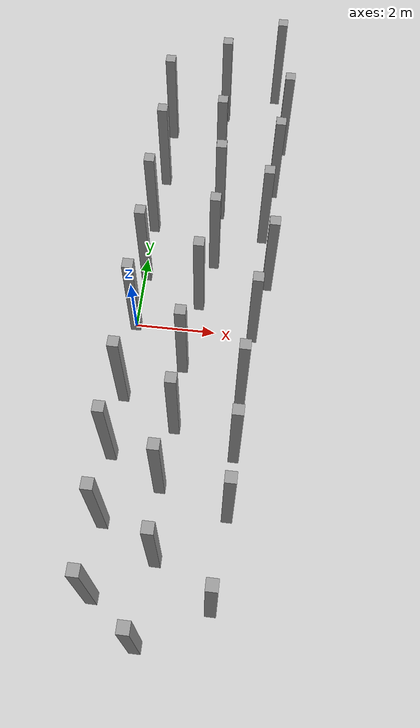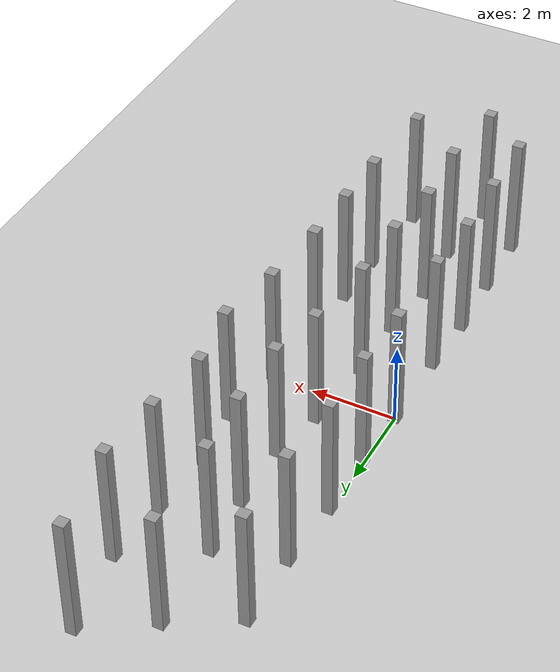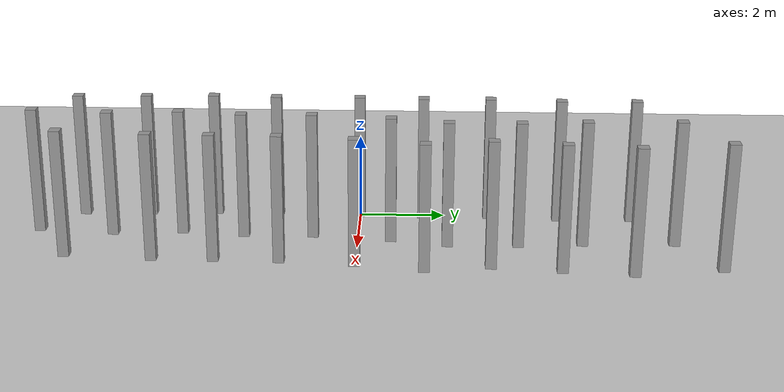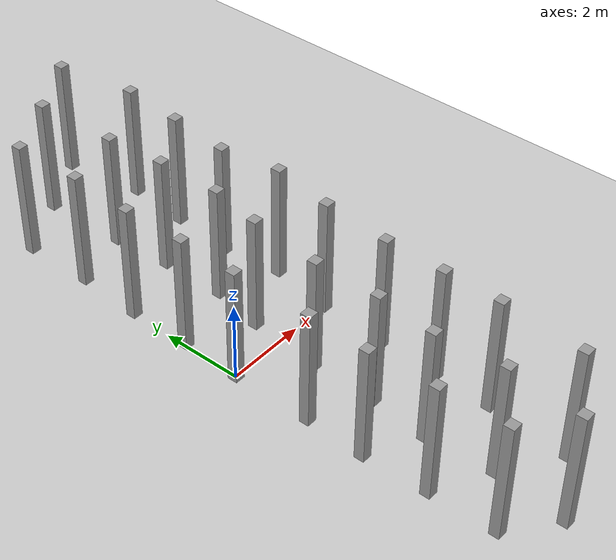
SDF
<sdf version="1.6">
 <world name="default">
  <light name="sun" type="directional">
   <pose>0 0 10 0 -0 0</pose>
   <diffuse>0.8 0.8 0.8 1</diffuse>
   <specular>0.1 0.1 0.1 1</specular>
   <attenuation>
    <range>1000</range>
    <constant>0.9</constant>
    <linear>0.01</linear>
    <quadratic>0.001</quadratic>
   </attenuation>
   <direction>-0.5 0.5 -1</direction>
  </light>
  <model name="ground_plane">
   <static>1</static>
   <link name="link">
    <collision name="collision">
     <geometry><plane><normal>0 0 1</normal><size>100 100</size></plane></geometry>
     <surface><friction><ode><mu>100</mu><mu2>50</mu2></ode></friction></surface>
    </collision>
    <visual name="visual">
     <cast_shadows>0</cast_shadows>
     <geometry><plane><normal>0 0 1</normal><size>100 100</size></plane></geometry>
     <material>
      <script><uri>file://media/materials/scripts/gazebo.material</uri><name>Gazebo/Grey</name></script>
     </material>
    </visual>
   </link>
  </model>
  <gravity>0 0 -9.8</gravity>
  <magnetic_field>6e-06 2.3e-05 -4.2e-05</magnetic_field>
  <atmosphere type="adiabatic"/>
  <physics name="default_physics" default="0" type="ode">
   <max_step_size>0.001</max_step_size>
   <real_time_factor>1</real_time_factor>
   <real_time_update_rate>1000</real_time_update_rate>
  </physics>
  <scene><ambient>0.4 0.4 0.4 1</ambient><background>0.7 0.7 0.7 1</background><shadows>1</shadows></scene>
  <spherical_coordinates>
   <surface_model>EARTH_WGS84</surface_model>
   <latitude_deg>0</latitude_deg>
   <longitude_deg>0</longitude_deg>
   <elevation>0</elevation>
   <heading_deg>0</heading_deg>
  </spherical_coordinates>
  <model name="box_2">
   <link name="link">
    <pose>0 0 1 0 -0 0</pose>
    <inertial>
     <mass>1</mass>
     <inertia><ixx>5.16667</ixx><ixy>0</ixy><ixz>0</ixz><iyy>5.16667</iyy><iyz>0</iyz><izz>5.16667</izz></inertia>
     <pose>0 0 1 0 -0 0</pose>
    </inertial>
    <visual name="ModelPreview_4::link::visual_1">
     <geometry><box><size>0.25 0.25 3</size></box></geometry>
     <material>
      <script><name>Gazebo/Grey</name><uri>file://media/materials/scripts/gazebo.material</uri></script>
      <ambient>0.3 0.3 0.3 1</ambient>
      <diffuse>0.7 0.7 0.7 1</diffuse>
      <specular>0.01 0.01 0.01 1</specular>
      <emissive>0 0 0 1</emissive>
      <shader type="vertex"><normal_map>__default__</normal_map></shader>
     </material>
    </visual>
    <visual name="visual">
     <geometry><box><size>0.25 0.25 3</size></box></geometry>
     <material>
      <script><name>Gazebo/Grey</name><uri>file://media/materials/scripts/gazebo.material</uri></script>
      <ambient>0.3 0.3 0.3 1</ambient>
      <diffuse>0.7 0.7 0.7 1</diffuse>
      <specular>0.01 0.01 0.01 1</specular>
      <emissive>0 0 0 1</emissive>
      <shader type="vertex"><normal_map>__default__</normal_map></shader>
     </material>
    </visual>
    <collision name="collision">
     <geometry><box><size>0.25 0.25 3</size></box></geometry>
     <surface>
      <friction>
       <ode><mu>1</mu><mu2>1</mu2><fdir1>0 0 0</fdir1><slip1>0</slip1><slip2>0</slip2></ode>
       <torsional>
        <coefficient>1</coefficient>
        <patch_radius>0</patch_radius>
        <surface_radius>0</surface_radius>
        <use_patch_radius>1</use_patch_radius>
        <ode><slip>0</slip></ode>
       </torsional>
      </friction>
      <bounce><restitution_coefficient>0</restitution_coefficient><threshold>1e+06</threshold></bounce>
      <contact>
       <collide_without_contact>0</collide_without_contact>
       <collide_without_contact_bitmask>1</collide_without_contact_bitmask>
       <collide_bitmask>1</collide_bitmask>
       <ode>
        <soft_cfm>0</soft_cfm>
        <soft_erp>0.2</soft_erp>
        <kp>1e+13</kp>
        <kd>1</kd>
        <max_vel>0.01</max_vel>
        <min_depth>0</min_depth>
       </ode>
       <bullet>
        <split_impulse>1</split_impulse>
        <split_impulse_penetration_threshold>-0.01</split_impulse_penetration_threshold>
        <soft_cfm>0</soft_cfm>
        <soft_erp>0.2</soft_erp>
        <kp>1e+13</kp>
        <kd>1</kd>
       </bullet>
      </contact>
     </surface>
    </collision>
   </link>
   <static>0</static>
   <pose>0.001306 -0.012782 0.5 0 0 -0.000121</pose>
  </model>
  <model name="box_2_0">
   <link name="link">
    <pose>0 0 1 0 -0 0</pose>
    <inertial>
     <mass>1</mass>
     <inertia><ixx>5.16667</ixx><ixy>0</ixy><ixz>0</ixz><iyy>5.16667</iyy><iyz>0</iyz><izz>5.16667</izz></inertia>
     <pose>0 0 1 0 -0 0</pose>
    </inertial>
    <visual name="ModelPreview_4::link::visual_1">
     <geometry><box><size>0.25 0.25 3</size></box></geometry>
     <material>
      <script><name>Gazebo/Grey</name><uri>file://media/materials/scripts/gazebo.material</uri></script>
      <ambient>0.3 0.3 0.3 1</ambient>
      <diffuse>0.7 0.7 0.7 1</diffuse>
      <specular>0.01 0.01 0.01 1</specular>
      <emissive>0 0 0 1</emissive>
      <shader type="vertex"><normal_map>__default__</normal_map></shader>
     </material>
    </visual>
    <visual name="visual">
     <geometry><box><size>0.25 0.25 3</size></box></geometry>
     <material>
      <script><name>Gazebo/Grey</name><uri>file://media/materials/scripts/gazebo.material</uri></script>
      <ambient>0.3 0.3 0.3 1</ambient>
      <diffuse>0.7 0.7 0.7 1</diffuse>
      <specular>0.01 0.01 0.01 1</specular>
      <emissive>0 0 0 1</emissive>
      <shader type="vertex"><normal_map>__default__</normal_map></shader>
     </material>
    </visual>
    <collision name="collision">
     <geometry><box><size>0.25 0.25 3</size></box></geometry>
     <surface>
      <friction>
       <ode><mu>1</mu><mu2>1</mu2><fdir1>0 0 0</fdir1><slip1>0</slip1><slip2>0</slip2></ode>
       <torsional>
        <coefficient>1</coefficient>
        <patch_radius>0</patch_radius>
        <surface_radius>0</surface_radius>
        <use_patch_radius>1</use_patch_radius>
        <ode><slip>0</slip></ode>
       </torsional>
      </friction>
      <bounce><restitution_coefficient>0</restitution_coefficient><threshold>1e+06</threshold></bounce>
      <contact>
       <collide_without_contact>0</collide_without_contact>
       <collide_without_contact_bitmask>1</collide_without_contact_bitmask>
       <collide_bitmask>1</collide_bitmask>
       <ode>
        <soft_cfm>0</soft_cfm>
        <soft_erp>0.2</soft_erp>
        <kp>1e+13</kp>
        <kd>1</kd>
        <max_vel>0.01</max_vel>
        <min_depth>0</min_depth>
       </ode>
       <bullet>
        <split_impulse>1</split_impulse>
        <split_impulse_penetration_threshold>-0.01</split_impulse_penetration_threshold>
        <soft_cfm>0</soft_cfm>
        <soft_erp>0.2</soft_erp>
        <kp>1e+13</kp>
        <kd>1</kd>
       </bullet>
      </contact>
     </surface>
    </collision>
   </link>
   <static>0</static>
   <pose>0.016184 -1.98397 0.5 -2e-06 -0 -0.000223</pose>
  </model>
  <model name="box_2_clone">
   <link name="link">
    <pose>0 0 1 0 -0 0</pose>
    <inertial>
     <mass>1</mass>
     <inertia><ixx>5.16667</ixx><ixy>0</ixy><ixz>0</ixz><iyy>5.16667</iyy><iyz>0</iyz><izz>5.16667</izz></inertia>
     <pose>0 0 1 0 -0 0</pose>
    </inertial>
    <visual name="ModelPreview_4::link::visual_1">
     <geometry><box><size>0.25 0.25 3</size></box></geometry>
     <material>
      <script><name>Gazebo/Grey</name><uri>file://media/materials/scripts/gazebo.material</uri></script>
      <ambient>0.3 0.3 0.3 1</ambient>
      <diffuse>0.7 0.7 0.7 1</diffuse>
      <specular>0.01 0.01 0.01 1</specular>
      <emissive>0 0 0 1</emissive>
      <shader type="vertex"><normal_map>__default__</normal_map></shader>
     </material>
    </visual>
    <visual name="visual">
     <geometry><box><size>0.25 0.25 3</size></box></geometry>
     <material>
      <script><name>Gazebo/Grey</name><uri>file://media/materials/scripts/gazebo.material</uri></script>
      <ambient>0.3 0.3 0.3 1</ambient>
      <diffuse>0.7 0.7 0.7 1</diffuse>
      <specular>0.01 0.01 0.01 1</specular>
      <emissive>0 0 0 1</emissive>
      <shader type="vertex"><normal_map>__default__</normal_map></shader>
     </material>
    </visual>
    <collision name="collision">
     <geometry><box><size>0.25 0.25 3</size></box></geometry>
     <surface>
      <friction>
       <ode><mu>1</mu><mu2>1</mu2><fdir1>0 0 0</fdir1><slip1>0</slip1><slip2>0</slip2></ode>
       <torsional>
        <coefficient>1</coefficient>
        <patch_radius>0</patch_radius>
        <surface_radius>0</surface_radius>
        <use_patch_radius>1</use_patch_radius>
        <ode><slip>0</slip></ode>
       </torsional>
      </friction>
      <bounce><restitution_coefficient>0</restitution_coefficient><threshold>1e+06</threshold></bounce>
      <contact>
       <collide_without_contact>0</collide_without_contact>
       <collide_without_contact_bitmask>1</collide_without_contact_bitmask>
       <collide_bitmask>1</collide_bitmask>
       <ode>
        <soft_cfm>0</soft_cfm>
        <soft_erp>0.2</soft_erp>
        <kp>1e+13</kp>
        <kd>1</kd>
        <max_vel>0.01</max_vel>
        <min_depth>0</min_depth>
       </ode>
       <bullet>
        <split_impulse>1</split_impulse>
        <split_impulse_penetration_threshold>-0.01</split_impulse_penetration_threshold>
        <soft_cfm>0</soft_cfm>
        <soft_erp>0.2</soft_erp>
        <kp>1e+13</kp>
        <kd>1</kd>
       </bullet>
      </contact>
     </surface>
    </collision>
   </link>
   <static>0</static>
   <pose>-0.030827 -3.47145 0.5 -2e-06 -0 -0.000164</pose>
  </model>
  <model name="box_2_clone_0">
   <link name="link">
    <pose>0 0 1 0 -0 0</pose>
    <inertial>
     <mass>1</mass>
     <inertia><ixx>5.16667</ixx><ixy>0</ixy><ixz>0</ixz><iyy>5.16667</iyy><iyz>0</iyz><izz>5.16667</izz></inertia>
     <pose>0 0 1 0 -0 0</pose>
    </inertial>
    <visual name="ModelPreview_4::link::visual_1">
     <geometry><box><size>0.25 0.25 3</size></box></geometry>
     <material>
      <script><name>Gazebo/Grey</name><uri>file://media/materials/scripts/gazebo.material</uri></script>
      <ambient>0.3 0.3 0.3 1</ambient>
      <diffuse>0.7 0.7 0.7 1</diffuse>
      <specular>0.01 0.01 0.01 1</specular>
      <emissive>0 0 0 1</emissive>
      <shader type="vertex"><normal_map>__default__</normal_map></shader>
     </material>
    </visual>
    <visual name="visual">
     <geometry><box><size>0.25 0.25 3</size></box></geometry>
     <material>
      <script><name>Gazebo/Grey</name><uri>file://media/materials/scripts/gazebo.material</uri></script>
      <ambient>0.3 0.3 0.3 1</ambient>
      <diffuse>0.7 0.7 0.7 1</diffuse>
      <specular>0.01 0.01 0.01 1</specular>
      <emissive>0 0 0 1</emissive>
      <shader type="vertex"><normal_map>__default__</normal_map></shader>
     </material>
    </visual>
    <collision name="collision">
     <geometry><box><size>0.25 0.25 3</size></box></geometry>
     <surface>
      <friction>
       <ode><mu>1</mu><mu2>1</mu2><fdir1>0 0 0</fdir1><slip1>0</slip1><slip2>0</slip2></ode>
       <torsional>
        <coefficient>1</coefficient>
        <patch_radius>0</patch_radius>
        <surface_radius>0</surface_radius>
        <use_patch_radius>1</use_patch_radius>
        <ode><slip>0</slip></ode>
       </torsional>
      </friction>
      <bounce><restitution_coefficient>0</restitution_coefficient><threshold>1e+06</threshold></bounce>
      <contact>
       <collide_without_contact>0</collide_without_contact>
       <collide_without_contact_bitmask>1</collide_without_contact_bitmask>
       <collide_bitmask>1</collide_bitmask>
       <ode>
        <soft_cfm>0</soft_cfm>
        <soft_erp>0.2</soft_erp>
        <kp>1e+13</kp>
        <kd>1</kd>
        <max_vel>0.01</max_vel>
        <min_depth>0</min_depth>
       </ode>
       <bullet>
        <split_impulse>1</split_impulse>
        <split_impulse_penetration_threshold>-0.01</split_impulse_penetration_threshold>
        <soft_cfm>0</soft_cfm>
        <soft_erp>0.2</soft_erp>
        <kp>1e+13</kp>
        <kd>1</kd>
       </bullet>
      </contact>
     </surface>
    </collision>
   </link>
   <static>0</static>
   <pose>0.044164 -5.06379 0.5 2e-06 -1e-06 -0.00013</pose>
  </model>
  <model name="box_2_clone_1">
   <link name="link">
    <pose>0 0 1 0 -0 0</pose>
    <inertial>
     <mass>1</mass>
     <inertia><ixx>5.16667</ixx><ixy>0</ixy><ixz>0</ixz><iyy>5.16667</iyy><iyz>0</iyz><izz>5.16667</izz></inertia>
     <pose>0 0 1 0 -0 0</pose>
    </inertial>
    <visual name="ModelPreview_4::link::visual_1">
     <geometry><box><size>0.25 0.25 3</size></box></geometry>
     <material>
      <script><name>Gazebo/Grey</name><uri>file://media/materials/scripts/gazebo.material</uri></script>
      <ambient>0.3 0.3 0.3 1</ambient>
      <diffuse>0.7 0.7 0.7 1</diffuse>
      <specular>0.01 0.01 0.01 1</specular>
      <emissive>0 0 0 1</emissive>
      <shader type="vertex"><normal_map>__default__</normal_map></shader>
     </material>
    </visual>
    <visual name="visual">
     <geometry><box><size>0.25 0.25 3</size></box></geometry>
     <material>
      <script><name>Gazebo/Grey</name><uri>file://media/materials/scripts/gazebo.material</uri></script>
      <ambient>0.3 0.3 0.3 1</ambient>
      <diffuse>0.7 0.7 0.7 1</diffuse>
      <specular>0.01 0.01 0.01 1</specular>
      <emissive>0 0 0 1</emissive>
      <shader type="vertex"><normal_map>__default__</normal_map></shader>
     </material>
    </visual>
    <collision name="collision">
     <geometry><box><size>0.25 0.25 3</size></box></geometry>
     <surface>
      <friction>
       <ode><mu>1</mu><mu2>1</mu2><fdir1>0 0 0</fdir1><slip1>0</slip1><slip2>0</slip2></ode>
       <torsional>
        <coefficient>1</coefficient>
        <patch_radius>0</patch_radius>
        <surface_radius>0</surface_radius>
        <use_patch_radius>1</use_patch_radius>
        <ode><slip>0</slip></ode>
       </torsional>
      </friction>
      <bounce><restitution_coefficient>0</restitution_coefficient><threshold>1e+06</threshold></bounce>
      <contact>
       <collide_without_contact>0</collide_without_contact>
       <collide_without_contact_bitmask>1</collide_without_contact_bitmask>
       <collide_bitmask>1</collide_bitmask>
       <ode>
        <soft_cfm>0</soft_cfm>
        <soft_erp>0.2</soft_erp>
        <kp>1e+13</kp>
        <kd>1</kd>
        <max_vel>0.01</max_vel>
        <min_depth>0</min_depth>
       </ode>
       <bullet>
        <split_impulse>1</split_impulse>
        <split_impulse_penetration_threshold>-0.01</split_impulse_penetration_threshold>
        <soft_cfm>0</soft_cfm>
        <soft_erp>0.2</soft_erp>
        <kp>1e+13</kp>
        <kd>1</kd>
       </bullet>
      </contact>
     </surface>
    </collision>
   </link>
   <static>0</static>
   <pose>0.048313 1.49751 0.5 0 0 -0.000186</pose>
  </model>
  <model name="box_2_clone_2">
   <link name="link">
    <pose>0 0 1 0 -0 0</pose>
    <inertial>
     <mass>1</mass>
     <inertia><ixx>5.16667</ixx><ixy>0</ixy><ixz>0</ixz><iyy>5.16667</iyy><iyz>0</iyz><izz>5.16667</izz></inertia>
     <pose>0 0 1 0 -0 0</pose>
    </inertial>
    <visual name="ModelPreview_4::link::visual_1">
     <geometry><box><size>0.25 0.25 3</size></box></geometry>
     <material>
      <script><name>Gazebo/Grey</name><uri>file://media/materials/scripts/gazebo.material</uri></script>
      <ambient>0.3 0.3 0.3 1</ambient>
      <diffuse>0.7 0.7 0.7 1</diffuse>
      <specular>0.01 0.01 0.01 1</specular>
      <emissive>0 0 0 1</emissive>
      <shader type="vertex"><normal_map>__default__</normal_map></shader>
     </material>
    </visual>
    <visual name="visual">
     <geometry><box><size>0.25 0.25 3</size></box></geometry>
     <material>
      <script><name>Gazebo/Grey</name><uri>file://media/materials/scripts/gazebo.material</uri></script>
      <ambient>0.3 0.3 0.3 1</ambient>
      <diffuse>0.7 0.7 0.7 1</diffuse>
      <specular>0.01 0.01 0.01 1</specular>
      <emissive>0 0 0 1</emissive>
      <shader type="vertex"><normal_map>__default__</normal_map></shader>
     </material>
    </visual>
    <collision name="collision">
     <geometry><box><size>0.25 0.25 3</size></box></geometry>
     <surface>
      <friction>
       <ode><mu>1</mu><mu2>1</mu2><fdir1>0 0 0</fdir1><slip1>0</slip1><slip2>0</slip2></ode>
       <torsional>
        <coefficient>1</coefficient>
        <patch_radius>0</patch_radius>
        <surface_radius>0</surface_radius>
        <use_patch_radius>1</use_patch_radius>
        <ode><slip>0</slip></ode>
       </torsional>
      </friction>
      <bounce><restitution_coefficient>0</restitution_coefficient><threshold>1e+06</threshold></bounce>
      <contact>
       <collide_without_contact>0</collide_without_contact>
       <collide_without_contact_bitmask>1</collide_without_contact_bitmask>
       <collide_bitmask>1</collide_bitmask>
       <ode>
        <soft_cfm>0</soft_cfm>
        <soft_erp>0.2</soft_erp>
        <kp>1e+13</kp>
        <kd>1</kd>
        <max_vel>0.01</max_vel>
        <min_depth>0</min_depth>
       </ode>
       <bullet>
        <split_impulse>1</split_impulse>
        <split_impulse_penetration_threshold>-0.01</split_impulse_penetration_threshold>
        <soft_cfm>0</soft_cfm>
        <soft_erp>0.2</soft_erp>
        <kp>1e+13</kp>
        <kd>1</kd>
       </bullet>
      </contact>
     </surface>
    </collision>
   </link>
   <static>0</static>
   <pose>0.031845 3.07004 0.5 0 0 -0.000171</pose>
  </model>
  <model name="box_2_clone_3">
   <link name="link">
    <pose>0 0 1 0 -0 0</pose>
    <inertial>
     <mass>1</mass>
     <inertia><ixx>5.16667</ixx><ixy>0</ixy><ixz>0</ixz><iyy>5.16667</iyy><iyz>0</iyz><izz>5.16667</izz></inertia>
     <pose>0 0 1 0 -0 0</pose>
    </inertial>
    <visual name="ModelPreview_4::link::visual_1">
     <geometry><box><size>0.25 0.25 3</size></box></geometry>
     <material>
      <script><name>Gazebo/Grey</name><uri>file://media/materials/scripts/gazebo.material</uri></script>
      <ambient>0.3 0.3 0.3 1</ambient>
      <diffuse>0.7 0.7 0.7 1</diffuse>
      <specular>0.01 0.01 0.01 1</specular>
      <emissive>0 0 0 1</emissive>
      <shader type="vertex"><normal_map>__default__</normal_map></shader>
     </material>
    </visual>
    <visual name="visual">
     <geometry><box><size>0.25 0.25 3</size></box></geometry>
     <material>
      <script><name>Gazebo/Grey</name><uri>file://media/materials/scripts/gazebo.material</uri></script>
      <ambient>0.3 0.3 0.3 1</ambient>
      <diffuse>0.7 0.7 0.7 1</diffuse>
      <specular>0.01 0.01 0.01 1</specular>
      <emissive>0 0 0 1</emissive>
      <shader type="vertex"><normal_map>__default__</normal_map></shader>
     </material>
    </visual>
    <collision name="collision">
     <geometry><box><size>0.25 0.25 3</size></box></geometry>
     <surface>
      <friction>
       <ode><mu>1</mu><mu2>1</mu2><fdir1>0 0 0</fdir1><slip1>0</slip1><slip2>0</slip2></ode>
       <torsional>
        <coefficient>1</coefficient>
        <patch_radius>0</patch_radius>
        <surface_radius>0</surface_radius>
        <use_patch_radius>1</use_patch_radius>
        <ode><slip>0</slip></ode>
       </torsional>
      </friction>
      <bounce><restitution_coefficient>0</restitution_coefficient><threshold>1e+06</threshold></bounce>
      <contact>
       <collide_without_contact>0</collide_without_contact>
       <collide_without_contact_bitmask>1</collide_without_contact_bitmask>
       <collide_bitmask>1</collide_bitmask>
       <ode>
        <soft_cfm>0</soft_cfm>
        <soft_erp>0.2</soft_erp>
        <kp>1e+13</kp>
        <kd>1</kd>
        <max_vel>0.01</max_vel>
        <min_depth>0</min_depth>
       </ode>
       <bullet>
        <split_impulse>1</split_impulse>
        <split_impulse_penetration_threshold>-0.01</split_impulse_penetration_threshold>
        <soft_cfm>0</soft_cfm>
        <soft_erp>0.2</soft_erp>
        <kp>1e+13</kp>
        <kd>1</kd>
       </bullet>
      </contact>
     </surface>
    </collision>
   </link>
   <static>0</static>
   <pose>0.124936 4.72453 0.500001 1e-06 3e-06 -9.4e-05</pose>
  </model>
  <model name="box_2_clone_4">
   <link name="link">
    <pose>0 0 1 0 -0 0</pose>
    <inertial>
     <mass>1</mass>
     <inertia><ixx>5.16667</ixx><ixy>0</ixy><ixz>0</ixz><iyy>5.16667</iyy><iyz>0</iyz><izz>5.16667</izz></inertia>
     <pose>0 0 1 0 -0 0</pose>
    </inertial>
    <visual name="ModelPreview_4::link::visual_1">
     <geometry><box><size>0.25 0.25 3</size></box></geometry>
     <material>
      <script><name>Gazebo/Grey</name><uri>file://media/materials/scripts/gazebo.material</uri></script>
      <ambient>0.3 0.3 0.3 1</ambient>
      <diffuse>0.7 0.7 0.7 1</diffuse>
      <specular>0.01 0.01 0.01 1</specular>
      <emissive>0 0 0 1</emissive>
      <shader type="vertex"><normal_map>__default__</normal_map></shader>
     </material>
    </visual>
    <visual name="visual">
     <geometry><box><size>0.25 0.25 3</size></box></geometry>
     <material>
      <script><name>Gazebo/Grey</name><uri>file://media/materials/scripts/gazebo.material</uri></script>
      <ambient>0.3 0.3 0.3 1</ambient>
      <diffuse>0.7 0.7 0.7 1</diffuse>
      <specular>0.01 0.01 0.01 1</specular>
      <emissive>0 0 0 1</emissive>
      <shader type="vertex"><normal_map>__default__</normal_map></shader>
     </material>
    </visual>
    <collision name="collision">
     <geometry><box><size>0.25 0.25 3</size></box></geometry>
     <surface>
      <friction>
       <ode><mu>1</mu><mu2>1</mu2><fdir1>0 0 0</fdir1><slip1>0</slip1><slip2>0</slip2></ode>
       <torsional>
        <coefficient>1</coefficient>
        <patch_radius>0</patch_radius>
        <surface_radius>0</surface_radius>
        <use_patch_radius>1</use_patch_radius>
        <ode><slip>0</slip></ode>
       </torsional>
      </friction>
      <bounce><restitution_coefficient>0</restitution_coefficient><threshold>1e+06</threshold></bounce>
      <contact>
       <collide_without_contact>0</collide_without_contact>
       <collide_without_contact_bitmask>1</collide_without_contact_bitmask>
       <collide_bitmask>1</collide_bitmask>
       <ode>
        <soft_cfm>0</soft_cfm>
        <soft_erp>0.2</soft_erp>
        <kp>1e+13</kp>
        <kd>1</kd>
        <max_vel>0.01</max_vel>
        <min_depth>0</min_depth>
       </ode>
       <bullet>
        <split_impulse>1</split_impulse>
        <split_impulse_penetration_threshold>-0.01</split_impulse_penetration_threshold>
        <soft_cfm>0</soft_cfm>
        <soft_erp>0.2</soft_erp>
        <kp>1e+13</kp>
        <kd>1</kd>
       </bullet>
      </contact>
     </surface>
    </collision>
   </link>
   <static>0</static>
   <pose>0.097978 6.47985 0.5 1e-06 -2e-06 -0.000149</pose>
  </model>
  <model name="box_2_clone_5">
   <link name="link">
    <pose>0 0 1 0 -0 0</pose>
    <inertial>
     <mass>1</mass>
     <inertia><ixx>5.16667</ixx><ixy>0</ixy><ixz>0</ixz><iyy>5.16667</iyy><iyz>0</iyz><izz>5.16667</izz></inertia>
     <pose>0 0 1 0 -0 0</pose>
    </inertial>
    <visual name="ModelPreview_4::link::visual_1">
     <geometry><box><size>0.25 0.25 3</size></box></geometry>
     <material>
      <script><name>Gazebo/Grey</name><uri>file://media/materials/scripts/gazebo.material</uri></script>
      <ambient>0.3 0.3 0.3 1</ambient>
      <diffuse>0.7 0.7 0.7 1</diffuse>
      <specular>0.01 0.01 0.01 1</specular>
      <emissive>0 0 0 1</emissive>
      <shader type="vertex"><normal_map>__default__</normal_map></shader>
     </material>
    </visual>
    <visual name="visual">
     <geometry><box><size>0.25 0.25 3</size></box></geometry>
     <material>
      <script><name>Gazebo/Grey</name><uri>file://media/materials/scripts/gazebo.material</uri></script>
      <ambient>0.3 0.3 0.3 1</ambient>
      <diffuse>0.7 0.7 0.7 1</diffuse>
      <specular>0.01 0.01 0.01 1</specular>
      <emissive>0 0 0 1</emissive>
      <shader type="vertex"><normal_map>__default__</normal_map></shader>
     </material>
    </visual>
    <collision name="collision">
     <geometry><box><size>0.25 0.25 3</size></box></geometry>
     <surface>
      <friction>
       <ode><mu>1</mu><mu2>1</mu2><fdir1>0 0 0</fdir1><slip1>0</slip1><slip2>0</slip2></ode>
       <torsional>
        <coefficient>1</coefficient>
        <patch_radius>0</patch_radius>
        <surface_radius>0</surface_radius>
        <use_patch_radius>1</use_patch_radius>
        <ode><slip>0</slip></ode>
       </torsional>
      </friction>
      <bounce><restitution_coefficient>0</restitution_coefficient><threshold>1e+06</threshold></bounce>
      <contact>
       <collide_without_contact>0</collide_without_contact>
       <collide_without_contact_bitmask>1</collide_without_contact_bitmask>
       <collide_bitmask>1</collide_bitmask>
       <ode>
        <soft_cfm>0</soft_cfm>
        <soft_erp>0.2</soft_erp>
        <kp>1e+13</kp>
        <kd>1</kd>
        <max_vel>0.01</max_vel>
        <min_depth>0</min_depth>
       </ode>
       <bullet>
        <split_impulse>1</split_impulse>
        <split_impulse_penetration_threshold>-0.01</split_impulse_penetration_threshold>
        <soft_cfm>0</soft_cfm>
        <soft_erp>0.2</soft_erp>
        <kp>1e+13</kp>
        <kd>1</kd>
       </bullet>
      </contact>
     </surface>
    </collision>
   </link>
   <static>0</static>
   <pose>0.096291 -6.6736 0.5 -2e-06 -1e-06 -9.9e-05</pose>
  </model>
  <model name="box_2_clone_1_clone">
   <link name="link">
    <pose>0 0 1 0 -0 0</pose>
    <inertial>
     <mass>1</mass>
     <inertia><ixx>5.16667</ixx><ixy>0</ixy><ixz>0</ixz><iyy>5.16667</iyy><iyz>0</iyz><izz>5.16667</izz></inertia>
     <pose>0 0 1 0 -0 0</pose>
    </inertial>
    <visual name="ModelPreview_4::link::visual_1">
     <geometry><box><size>0.25 0.25 3</size></box></geometry>
     <material>
      <script><name>Gazebo/Grey</name><uri>file://media/materials/scripts/gazebo.material</uri></script>
      <ambient>0.3 0.3 0.3 1</ambient>
      <diffuse>0.7 0.7 0.7 1</diffuse>
      <specular>0.01 0.01 0.01 1</specular>
      <emissive>0 0 0 1</emissive>
      <shader type="vertex"><normal_map>__default__</normal_map></shader>
     </material>
    </visual>
    <visual name="visual">
     <geometry><box><size>0.25 0.25 3</size></box></geometry>
     <material>
      <script><name>Gazebo/Grey</name><uri>file://media/materials/scripts/gazebo.material</uri></script>
      <ambient>0.3 0.3 0.3 1</ambient>
      <diffuse>0.7 0.7 0.7 1</diffuse>
      <specular>0.01 0.01 0.01 1</specular>
      <emissive>0 0 0 1</emissive>
      <shader type="vertex"><normal_map>__default__</normal_map></shader>
     </material>
    </visual>
    <collision name="collision">
     <geometry><box><size>0.25 0.25 3</size></box></geometry>
     <surface>
      <friction>
       <ode><mu>1</mu><mu2>1</mu2><fdir1>0 0 0</fdir1><slip1>0</slip1><slip2>0</slip2></ode>
       <torsional>
        <coefficient>1</coefficient>
        <patch_radius>0</patch_radius>
        <surface_radius>0</surface_radius>
        <use_patch_radius>1</use_patch_radius>
        <ode><slip>0</slip></ode>
       </torsional>
      </friction>
      <bounce><restitution_coefficient>0</restitution_coefficient><threshold>1e+06</threshold></bounce>
      <contact>
       <collide_without_contact>0</collide_without_contact>
       <collide_without_contact_bitmask>1</collide_without_contact_bitmask>
       <collide_bitmask>1</collide_bitmask>
       <ode>
        <soft_cfm>0</soft_cfm>
        <soft_erp>0.2</soft_erp>
        <kp>1e+13</kp>
        <kd>1</kd>
        <max_vel>0.01</max_vel>
        <min_depth>0</min_depth>
       </ode>
       <bullet>
        <split_impulse>1</split_impulse>
        <split_impulse_penetration_threshold>-0.01</split_impulse_penetration_threshold>
        <soft_cfm>0</soft_cfm>
        <soft_erp>0.2</soft_erp>
        <kp>1e+13</kp>
        <kd>1</kd>
       </bullet>
      </contact>
     </surface>
    </collision>
   </link>
   <static>0</static>
   <pose>1.77319 2.07182 0.5 1e-06 -0 -0.000176</pose>
  </model>
  <model name="box_2_clone_1_clone_0">
   <link name="link">
    <pose>0 0 1 0 -0 0</pose>
    <inertial>
     <mass>1</mass>
     <inertia><ixx>5.16667</ixx><ixy>0</ixy><ixz>0</ixz><iyy>5.16667</iyy><iyz>0</iyz><izz>5.16667</izz></inertia>
     <pose>0 0 1 0 -0 0</pose>
    </inertial>
    <visual name="ModelPreview_4::link::visual_1">
     <geometry><box><size>0.25 0.25 3</size></box></geometry>
     <material>
      <script><name>Gazebo/Grey</name><uri>file://media/materials/scripts/gazebo.material</uri></script>
      <ambient>0.3 0.3 0.3 1</ambient>
      <diffuse>0.7 0.7 0.7 1</diffuse>
      <specular>0.01 0.01 0.01 1</specular>
      <emissive>0 0 0 1</emissive>
      <shader type="vertex"><normal_map>__default__</normal_map></shader>
     </material>
    </visual>
    <visual name="visual">
     <geometry><box><size>0.25 0.25 3</size></box></geometry>
     <material>
      <script><name>Gazebo/Grey</name><uri>file://media/materials/scripts/gazebo.material</uri></script>
      <ambient>0.3 0.3 0.3 1</ambient>
      <diffuse>0.7 0.7 0.7 1</diffuse>
      <specular>0.01 0.01 0.01 1</specular>
      <emissive>0 0 0 1</emissive>
      <shader type="vertex"><normal_map>__default__</normal_map></shader>
     </material>
    </visual>
    <collision name="collision">
     <geometry><box><size>0.25 0.25 3</size></box></geometry>
     <surface>
      <friction>
       <ode><mu>1</mu><mu2>1</mu2><fdir1>0 0 0</fdir1><slip1>0</slip1><slip2>0</slip2></ode>
       <torsional>
        <coefficient>1</coefficient>
        <patch_radius>0</patch_radius>
        <surface_radius>0</surface_radius>
        <use_patch_radius>1</use_patch_radius>
        <ode><slip>0</slip></ode>
       </torsional>
      </friction>
      <bounce><restitution_coefficient>0</restitution_coefficient><threshold>1e+06</threshold></bounce>
      <contact>
       <collide_without_contact>0</collide_without_contact>
       <collide_without_contact_bitmask>1</collide_without_contact_bitmask>
       <collide_bitmask>1</collide_bitmask>
       <ode>
        <soft_cfm>0</soft_cfm>
        <soft_erp>0.2</soft_erp>
        <kp>1e+13</kp>
        <kd>1</kd>
        <max_vel>0.01</max_vel>
        <min_depth>0</min_depth>
       </ode>
       <bullet>
        <split_impulse>1</split_impulse>
        <split_impulse_penetration_threshold>-0.01</split_impulse_penetration_threshold>
        <soft_cfm>0</soft_cfm>
        <soft_erp>0.2</soft_erp>
        <kp>1e+13</kp>
        <kd>1</kd>
       </bullet>
      </contact>
     </surface>
    </collision>
   </link>
   <static>0</static>
   <pose>1.747 3.70529 0.5 -0 3e-06 -0.000185</pose>
  </model>
  <model name="box_2_clone_1_clone_1">
   <link name="link">
    <pose>0 0 1 0 -0 0</pose>
    <inertial>
     <mass>1</mass>
     <inertia><ixx>5.16667</ixx><ixy>0</ixy><ixz>0</ixz><iyy>5.16667</iyy><iyz>0</iyz><izz>5.16667</izz></inertia>
     <pose>0 0 1 0 -0 0</pose>
    </inertial>
    <visual name="ModelPreview_4::link::visual_1">
     <geometry><box><size>0.25 0.25 3</size></box></geometry>
     <material>
      <script><name>Gazebo/Grey</name><uri>file://media/materials/scripts/gazebo.material</uri></script>
      <ambient>0.3 0.3 0.3 1</ambient>
      <diffuse>0.7 0.7 0.7 1</diffuse>
      <specular>0.01 0.01 0.01 1</specular>
      <emissive>0 0 0 1</emissive>
      <shader type="vertex"><normal_map>__default__</normal_map></shader>
     </material>
    </visual>
    <visual name="visual">
     <geometry><box><size>0.25 0.25 3</size></box></geometry>
     <material>
      <script><name>Gazebo/Grey</name><uri>file://media/materials/scripts/gazebo.material</uri></script>
      <ambient>0.3 0.3 0.3 1</ambient>
      <diffuse>0.7 0.7 0.7 1</diffuse>
      <specular>0.01 0.01 0.01 1</specular>
      <emissive>0 0 0 1</emissive>
      <shader type="vertex"><normal_map>__default__</normal_map></shader>
     </material>
    </visual>
    <collision name="collision">
     <geometry><box><size>0.25 0.25 3</size></box></geometry>
     <surface>
      <friction>
       <ode><mu>1</mu><mu2>1</mu2><fdir1>0 0 0</fdir1><slip1>0</slip1><slip2>0</slip2></ode>
       <torsional>
        <coefficient>1</coefficient>
        <patch_radius>0</patch_radius>
        <surface_radius>0</surface_radius>
        <use_patch_radius>1</use_patch_radius>
        <ode><slip>0</slip></ode>
       </torsional>
      </friction>
      <bounce><restitution_coefficient>0</restitution_coefficient><threshold>1e+06</threshold></bounce>
      <contact>
       <collide_without_contact>0</collide_without_contact>
       <collide_without_contact_bitmask>1</collide_without_contact_bitmask>
       <collide_bitmask>1</collide_bitmask>
       <ode>
        <soft_cfm>0</soft_cfm>
        <soft_erp>0.2</soft_erp>
        <kp>1e+13</kp>
        <kd>1</kd>
        <max_vel>0.01</max_vel>
        <min_depth>0</min_depth>
       </ode>
       <bullet>
        <split_impulse>1</split_impulse>
        <split_impulse_penetration_threshold>-0.01</split_impulse_penetration_threshold>
        <soft_cfm>0</soft_cfm>
        <soft_erp>0.2</soft_erp>
        <kp>1e+13</kp>
        <kd>1</kd>
       </bullet>
      </contact>
     </surface>
    </collision>
   </link>
   <static>0</static>
   <pose>1.6256 5.19207 0.500001 -4e-06 -1e-06 -0.000196</pose>
  </model>
  <model name="box_2_clone_1_clone_2">
   <link name="link">
    <pose>0 0 1 0 -0 0</pose>
    <inertial>
     <mass>1</mass>
     <inertia><ixx>5.16667</ixx><ixy>0</ixy><ixz>0</ixz><iyy>5.16667</iyy><iyz>0</iyz><izz>5.16667</izz></inertia>
     <pose>0 0 1 0 -0 0</pose>
    </inertial>
    <visual name="ModelPreview_4::link::visual_1">
     <geometry><box><size>0.25 0.25 3</size></box></geometry>
     <material>
      <script><name>Gazebo/Grey</name><uri>file://media/materials/scripts/gazebo.material</uri></script>
      <ambient>0.3 0.3 0.3 1</ambient>
      <diffuse>0.7 0.7 0.7 1</diffuse>
      <specular>0.01 0.01 0.01 1</specular>
      <emissive>0 0 0 1</emissive>
      <shader type="vertex"><normal_map>__default__</normal_map></shader>
     </material>
    </visual>
    <visual name="visual">
     <geometry><box><size>0.25 0.25 3</size></box></geometry>
     <material>
      <script><name>Gazebo/Grey</name><uri>file://media/materials/scripts/gazebo.material</uri></script>
      <ambient>0.3 0.3 0.3 1</ambient>
      <diffuse>0.7 0.7 0.7 1</diffuse>
      <specular>0.01 0.01 0.01 1</specular>
      <emissive>0 0 0 1</emissive>
      <shader type="vertex"><normal_map>__default__</normal_map></shader>
     </material>
    </visual>
    <collision name="collision">
     <geometry><box><size>0.25 0.25 3</size></box></geometry>
     <surface>
      <friction>
       <ode><mu>1</mu><mu2>1</mu2><fdir1>0 0 0</fdir1><slip1>0</slip1><slip2>0</slip2></ode>
       <torsional>
        <coefficient>1</coefficient>
        <patch_radius>0</patch_radius>
        <surface_radius>0</surface_radius>
        <use_patch_radius>1</use_patch_radius>
        <ode><slip>0</slip></ode>
       </torsional>
      </friction>
      <bounce><restitution_coefficient>0</restitution_coefficient><threshold>1e+06</threshold></bounce>
      <contact>
       <collide_without_contact>0</collide_without_contact>
       <collide_without_contact_bitmask>1</collide_without_contact_bitmask>
       <collide_bitmask>1</collide_bitmask>
       <ode>
        <soft_cfm>0</soft_cfm>
        <soft_erp>0.2</soft_erp>
        <kp>1e+13</kp>
        <kd>1</kd>
        <max_vel>0.01</max_vel>
        <min_depth>0</min_depth>
       </ode>
       <bullet>
        <split_impulse>1</split_impulse>
        <split_impulse_penetration_threshold>-0.01</split_impulse_penetration_threshold>
        <soft_cfm>0</soft_cfm>
        <soft_erp>0.2</soft_erp>
        <kp>1e+13</kp>
        <kd>1</kd>
       </bullet>
      </contact>
     </surface>
    </collision>
   </link>
   <static>0</static>
   <pose>1.52668 0.763108 0.5 0 0 -0.000189</pose>
  </model>
  <model name="box_2_clone_1_clone_3">
   <link name="link">
    <pose>0 0 1 0 -0 0</pose>
    <inertial>
     <mass>1</mass>
     <inertia><ixx>5.16667</ixx><ixy>0</ixy><ixz>0</ixz><iyy>5.16667</iyy><iyz>0</iyz><izz>5.16667</izz></inertia>
     <pose>0 0 1 0 -0 0</pose>
    </inertial>
    <visual name="ModelPreview_4::link::visual_1">
     <geometry><box><size>0.25 0.25 3</size></box></geometry>
     <material>
      <script><name>Gazebo/Grey</name><uri>file://media/materials/scripts/gazebo.material</uri></script>
      <ambient>0.3 0.3 0.3 1</ambient>
      <diffuse>0.7 0.7 0.7 1</diffuse>
      <specular>0.01 0.01 0.01 1</specular>
      <emissive>0 0 0 1</emissive>
      <shader type="vertex"><normal_map>__default__</normal_map></shader>
     </material>
    </visual>
    <visual name="visual">
     <geometry><box><size>0.25 0.25 3</size></box></geometry>
     <material>
      <script><name>Gazebo/Grey</name><uri>file://media/materials/scripts/gazebo.material</uri></script>
      <ambient>0.3 0.3 0.3 1</ambient>
      <diffuse>0.7 0.7 0.7 1</diffuse>
      <specular>0.01 0.01 0.01 1</specular>
      <emissive>0 0 0 1</emissive>
      <shader type="vertex"><normal_map>__default__</normal_map></shader>
     </material>
    </visual>
    <collision name="collision">
     <geometry><box><size>0.25 0.25 3</size></box></geometry>
     <surface>
      <friction>
       <ode><mu>1</mu><mu2>1</mu2><fdir1>0 0 0</fdir1><slip1>0</slip1><slip2>0</slip2></ode>
       <torsional>
        <coefficient>1</coefficient>
        <patch_radius>0</patch_radius>
        <surface_radius>0</surface_radius>
        <use_patch_radius>1</use_patch_radius>
        <ode><slip>0</slip></ode>
       </torsional>
      </friction>
      <bounce><restitution_coefficient>0</restitution_coefficient><threshold>1e+06</threshold></bounce>
      <contact>
       <collide_without_contact>0</collide_without_contact>
       <collide_without_contact_bitmask>1</collide_without_contact_bitmask>
       <collide_bitmask>1</collide_bitmask>
       <ode>
        <soft_cfm>0</soft_cfm>
        <soft_erp>0.2</soft_erp>
        <kp>1e+13</kp>
        <kd>1</kd>
        <max_vel>0.01</max_vel>
        <min_depth>0</min_depth>
       </ode>
       <bullet>
        <split_impulse>1</split_impulse>
        <split_impulse_penetration_threshold>-0.01</split_impulse_penetration_threshold>
        <soft_cfm>0</soft_cfm>
        <soft_erp>0.2</soft_erp>
        <kp>1e+13</kp>
        <kd>1</kd>
       </bullet>
      </contact>
     </surface>
    </collision>
   </link>
   <static>0</static>
   <pose>1.33324 -1.05587 0.5 0 -2e-06 -0.000193</pose>
  </model>
  <model name="box_2_clone_1_clone_4">
   <link name="link">
    <pose>0 0 1 0 -0 0</pose>
    <inertial>
     <mass>1</mass>
     <inertia><ixx>5.16667</ixx><ixy>0</ixy><ixz>0</ixz><iyy>5.16667</iyy><iyz>0</iyz><izz>5.16667</izz></inertia>
     <pose>0 0 1 0 -0 0</pose>
    </inertial>
    <visual name="ModelPreview_4::link::visual_1">
     <geometry><box><size>0.25 0.25 3</size></box></geometry>
     <material>
      <script><name>Gazebo/Grey</name><uri>file://media/materials/scripts/gazebo.material</uri></script>
      <ambient>0.3 0.3 0.3 1</ambient>
      <diffuse>0.7 0.7 0.7 1</diffuse>
      <specular>0.01 0.01 0.01 1</specular>
      <emissive>0 0 0 1</emissive>
      <shader type="vertex"><normal_map>__default__</normal_map></shader>
     </material>
    </visual>
    <visual name="visual">
     <geometry><box><size>0.25 0.25 3</size></box></geometry>
     <material>
      <script><name>Gazebo/Grey</name><uri>file://media/materials/scripts/gazebo.material</uri></script>
      <ambient>0.3 0.3 0.3 1</ambient>
      <diffuse>0.7 0.7 0.7 1</diffuse>
      <specular>0.01 0.01 0.01 1</specular>
      <emissive>0 0 0 1</emissive>
      <shader type="vertex"><normal_map>__default__</normal_map></shader>
     </material>
    </visual>
    <collision name="collision">
     <geometry><box><size>0.25 0.25 3</size></box></geometry>
     <surface>
      <friction>
       <ode><mu>1</mu><mu2>1</mu2><fdir1>0 0 0</fdir1><slip1>0</slip1><slip2>0</slip2></ode>
       <torsional>
        <coefficient>1</coefficient>
        <patch_radius>0</patch_radius>
        <surface_radius>0</surface_radius>
        <use_patch_radius>1</use_patch_radius>
        <ode><slip>0</slip></ode>
       </torsional>
      </friction>
      <bounce><restitution_coefficient>0</restitution_coefficient><threshold>1e+06</threshold></bounce>
      <contact>
       <collide_without_contact>0</collide_without_contact>
       <collide_without_contact_bitmask>1</collide_without_contact_bitmask>
       <collide_bitmask>1</collide_bitmask>
       <ode>
        <soft_cfm>0</soft_cfm>
        <soft_erp>0.2</soft_erp>
        <kp>1e+13</kp>
        <kd>1</kd>
        <max_vel>0.01</max_vel>
        <min_depth>0</min_depth>
       </ode>
       <bullet>
        <split_impulse>1</split_impulse>
        <split_impulse_penetration_threshold>-0.01</split_impulse_penetration_threshold>
        <soft_cfm>0</soft_cfm>
        <soft_erp>0.2</soft_erp>
        <kp>1e+13</kp>
        <kd>1</kd>
       </bullet>
      </contact>
     </surface>
    </collision>
   </link>
   <static>0</static>
   <pose>1.34592 -2.67105 0.500001 0 -4e-06 -0.000177</pose>
  </model>
  <model name="box_2_clone_1_clone_5">
   <link name="link">
    <pose>0 0 1 0 -0 0</pose>
    <inertial>
     <mass>1</mass>
     <inertia><ixx>5.16667</ixx><ixy>0</ixy><ixz>0</ixz><iyy>5.16667</iyy><iyz>0</iyz><izz>5.16667</izz></inertia>
     <pose>0 0 1 0 -0 0</pose>
    </inertial>
    <visual name="ModelPreview_4::link::visual_1">
     <geometry><box><size>0.25 0.25 3</size></box></geometry>
     <material>
      <script><name>Gazebo/Grey</name><uri>file://media/materials/scripts/gazebo.material</uri></script>
      <ambient>0.3 0.3 0.3 1</ambient>
      <diffuse>0.7 0.7 0.7 1</diffuse>
      <specular>0.01 0.01 0.01 1</specular>
      <emissive>0 0 0 1</emissive>
      <shader type="vertex"><normal_map>__default__</normal_map></shader>
     </material>
    </visual>
    <visual name="visual">
     <geometry><box><size>0.25 0.25 3</size></box></geometry>
     <material>
      <script><name>Gazebo/Grey</name><uri>file://media/materials/scripts/gazebo.material</uri></script>
      <ambient>0.3 0.3 0.3 1</ambient>
      <diffuse>0.7 0.7 0.7 1</diffuse>
      <specular>0.01 0.01 0.01 1</specular>
      <emissive>0 0 0 1</emissive>
      <shader type="vertex"><normal_map>__default__</normal_map></shader>
     </material>
    </visual>
    <collision name="collision">
     <geometry><box><size>0.25 0.25 3</size></box></geometry>
     <surface>
      <friction>
       <ode><mu>1</mu><mu2>1</mu2><fdir1>0 0 0</fdir1><slip1>0</slip1><slip2>0</slip2></ode>
       <torsional>
        <coefficient>1</coefficient>
        <patch_radius>0</patch_radius>
        <surface_radius>0</surface_radius>
        <use_patch_radius>1</use_patch_radius>
        <ode><slip>0</slip></ode>
       </torsional>
      </friction>
      <bounce><restitution_coefficient>0</restitution_coefficient><threshold>1e+06</threshold></bounce>
      <contact>
       <collide_without_contact>0</collide_without_contact>
       <collide_without_contact_bitmask>1</collide_without_contact_bitmask>
       <collide_bitmask>1</collide_bitmask>
       <ode>
        <soft_cfm>0</soft_cfm>
        <soft_erp>0.2</soft_erp>
        <kp>1e+13</kp>
        <kd>1</kd>
        <max_vel>0.01</max_vel>
        <min_depth>0</min_depth>
       </ode>
       <bullet>
        <split_impulse>1</split_impulse>
        <split_impulse_penetration_threshold>-0.01</split_impulse_penetration_threshold>
        <soft_cfm>0</soft_cfm>
        <soft_erp>0.2</soft_erp>
        <kp>1e+13</kp>
        <kd>1</kd>
       </bullet>
      </contact>
     </surface>
    </collision>
   </link>
   <static>0</static>
   <pose>1.2015 -4.12952 0.500001 4e-06 7e-06 -0.000131</pose>
  </model>
  <model name="box_2_clone_1_clone_6">
   <link name="link">
    <pose>0 0 1 0 -0 0</pose>
    <inertial>
     <mass>1</mass>
     <inertia><ixx>5.16667</ixx><ixy>0</ixy><ixz>0</ixz><iyy>5.16667</iyy><iyz>0</iyz><izz>5.16667</izz></inertia>
     <pose>0 0 1 0 -0 0</pose>
    </inertial>
    <visual name="ModelPreview_4::link::visual_1">
     <geometry><box><size>0.25 0.25 3</size></box></geometry>
     <material>
      <script><name>Gazebo/Grey</name><uri>file://media/materials/scripts/gazebo.material</uri></script>
      <ambient>0.3 0.3 0.3 1</ambient>
      <diffuse>0.7 0.7 0.7 1</diffuse>
      <specular>0.01 0.01 0.01 1</specular>
      <emissive>0 0 0 1</emissive>
      <shader type="vertex"><normal_map>__default__</normal_map></shader>
     </material>
    </visual>
    <visual name="visual">
     <geometry><box><size>0.25 0.25 3</size></box></geometry>
     <material>
      <script><name>Gazebo/Grey</name><uri>file://media/materials/scripts/gazebo.material</uri></script>
      <ambient>0.3 0.3 0.3 1</ambient>
      <diffuse>0.7 0.7 0.7 1</diffuse>
      <specular>0.01 0.01 0.01 1</specular>
      <emissive>0 0 0 1</emissive>
      <shader type="vertex"><normal_map>__default__</normal_map></shader>
     </material>
    </visual>
    <collision name="collision">
     <geometry><box><size>0.25 0.25 3</size></box></geometry>
     <surface>
      <friction>
       <ode><mu>1</mu><mu2>1</mu2><fdir1>0 0 0</fdir1><slip1>0</slip1><slip2>0</slip2></ode>
       <torsional>
        <coefficient>1</coefficient>
        <patch_radius>0</patch_radius>
        <surface_radius>0</surface_radius>
        <use_patch_radius>1</use_patch_radius>
        <ode><slip>0</slip></ode>
       </torsional>
      </friction>
      <bounce><restitution_coefficient>0</restitution_coefficient><threshold>1e+06</threshold></bounce>
      <contact>
       <collide_without_contact>0</collide_without_contact>
       <collide_without_contact_bitmask>1</collide_without_contact_bitmask>
       <collide_bitmask>1</collide_bitmask>
       <ode>
        <soft_cfm>0</soft_cfm>
        <soft_erp>0.2</soft_erp>
        <kp>1e+13</kp>
        <kd>1</kd>
        <max_vel>0.01</max_vel>
        <min_depth>0</min_depth>
       </ode>
       <bullet>
        <split_impulse>1</split_impulse>
        <split_impulse_penetration_threshold>-0.01</split_impulse_penetration_threshold>
        <soft_cfm>0</soft_cfm>
        <soft_erp>0.2</soft_erp>
        <kp>1e+13</kp>
        <kd>1</kd>
       </bullet>
      </contact>
     </surface>
    </collision>
   </link>
   <static>0</static>
   <pose>1.33407 -5.76082 0.500001 -4e-06 4e-06 -0.000178</pose>
  </model>
  <model name="box_2_clone_1_clone_7">
   <link name="link">
    <pose>0 0 1 0 -0 0</pose>
    <inertial>
     <mass>1</mass>
     <inertia><ixx>5.16667</ixx><ixy>0</ixy><ixz>0</ixz><iyy>5.16667</iyy><iyz>0</iyz><izz>5.16667</izz></inertia>
     <pose>0 0 1 0 -0 0</pose>
    </inertial>
    <visual name="ModelPreview_4::link::visual_1">
     <geometry><box><size>0.25 0.25 3</size></box></geometry>
     <material>
      <script><name>Gazebo/Grey</name><uri>file://media/materials/scripts/gazebo.material</uri></script>
      <ambient>0.3 0.3 0.3 1</ambient>
      <diffuse>0.7 0.7 0.7 1</diffuse>
      <specular>0.01 0.01 0.01 1</specular>
      <emissive>0 0 0 1</emissive>
      <shader type="vertex"><normal_map>__default__</normal_map></shader>
     </material>
    </visual>
    <visual name="visual">
     <geometry><box><size>0.25 0.25 3</size></box></geometry>
     <material>
      <script><name>Gazebo/Grey</name><uri>file://media/materials/scripts/gazebo.material</uri></script>
      <ambient>0.3 0.3 0.3 1</ambient>
      <diffuse>0.7 0.7 0.7 1</diffuse>
      <specular>0.01 0.01 0.01 1</specular>
      <emissive>0 0 0 1</emissive>
      <shader type="vertex"><normal_map>__default__</normal_map></shader>
     </material>
    </visual>
    <collision name="collision">
     <geometry><box><size>0.25 0.25 3</size></box></geometry>
     <surface>
      <friction>
       <ode><mu>1</mu><mu2>1</mu2><fdir1>0 0 0</fdir1><slip1>0</slip1><slip2>0</slip2></ode>
       <torsional>
        <coefficient>1</coefficient>
        <patch_radius>0</patch_radius>
        <surface_radius>0</surface_radius>
        <use_patch_radius>1</use_patch_radius>
        <ode><slip>0</slip></ode>
       </torsional>
      </friction>
      <bounce><restitution_coefficient>0</restitution_coefficient><threshold>1e+06</threshold></bounce>
      <contact>
       <collide_without_contact>0</collide_without_contact>
       <collide_without_contact_bitmask>1</collide_without_contact_bitmask>
       <collide_bitmask>1</collide_bitmask>
       <ode>
        <soft_cfm>0</soft_cfm>
        <soft_erp>0.2</soft_erp>
        <kp>1e+13</kp>
        <kd>1</kd>
        <max_vel>0.01</max_vel>
        <min_depth>0</min_depth>
       </ode>
       <bullet>
        <split_impulse>1</split_impulse>
        <split_impulse_penetration_threshold>-0.01</split_impulse_penetration_threshold>
        <soft_cfm>0</soft_cfm>
        <soft_erp>0.2</soft_erp>
        <kp>1e+13</kp>
        <kd>1</kd>
       </bullet>
      </contact>
     </surface>
    </collision>
   </link>
   <static>0</static>
   <pose>1.16884 -7.53019 0.5 0 0 -0.000139</pose>
  </model>
  <model name="box_2_clone_1_clone_8">
   <link name="link">
    <pose>0 0 1 0 -0 0</pose>
    <inertial>
     <mass>1</mass>
     <inertia><ixx>5.16667</ixx><ixy>0</ixy><ixz>0</ixz><iyy>5.16667</iyy><iyz>0</iyz><izz>5.16667</izz></inertia>
     <pose>0 0 1 0 -0 0</pose>
    </inertial>
    <visual name="ModelPreview_4::link::visual_1">
     <geometry><box><size>0.25 0.25 3</size></box></geometry>
     <material>
      <script><name>Gazebo/Grey</name><uri>file://media/materials/scripts/gazebo.material</uri></script>
      <ambient>0.3 0.3 0.3 1</ambient>
      <diffuse>0.7 0.7 0.7 1</diffuse>
      <specular>0.01 0.01 0.01 1</specular>
      <emissive>0 0 0 1</emissive>
      <shader type="vertex"><normal_map>__default__</normal_map></shader>
     </material>
    </visual>
    <visual name="visual">
     <geometry><box><size>0.25 0.25 3</size></box></geometry>
     <material>
      <script><name>Gazebo/Grey</name><uri>file://media/materials/scripts/gazebo.material</uri></script>
      <ambient>0.3 0.3 0.3 1</ambient>
      <diffuse>0.7 0.7 0.7 1</diffuse>
      <specular>0.01 0.01 0.01 1</specular>
      <emissive>0 0 0 1</emissive>
      <shader type="vertex"><normal_map>__default__</normal_map></shader>
     </material>
    </visual>
    <collision name="collision">
     <geometry><box><size>0.25 0.25 3</size></box></geometry>
     <surface>
      <friction>
       <ode><mu>1</mu><mu2>1</mu2><fdir1>0 0 0</fdir1><slip1>0</slip1><slip2>0</slip2></ode>
       <torsional>
        <coefficient>1</coefficient>
        <patch_radius>0</patch_radius>
        <surface_radius>0</surface_radius>
        <use_patch_radius>1</use_patch_radius>
        <ode><slip>0</slip></ode>
       </torsional>
      </friction>
      <bounce><restitution_coefficient>0</restitution_coefficient><threshold>1e+06</threshold></bounce>
      <contact>
       <collide_without_contact>0</collide_without_contact>
       <collide_without_contact_bitmask>1</collide_without_contact_bitmask>
       <collide_bitmask>1</collide_bitmask>
       <ode>
        <soft_cfm>0</soft_cfm>
        <soft_erp>0.2</soft_erp>
        <kp>1e+13</kp>
        <kd>1</kd>
        <max_vel>0.01</max_vel>
        <min_depth>0</min_depth>
       </ode>
       <bullet>
        <split_impulse>1</split_impulse>
        <split_impulse_penetration_threshold>-0.01</split_impulse_penetration_threshold>
        <soft_cfm>0</soft_cfm>
        <soft_erp>0.2</soft_erp>
        <kp>1e+13</kp>
        <kd>1</kd>
       </bullet>
      </contact>
     </surface>
    </collision>
   </link>
   <static>0</static>
   <pose>1.54617 7.31486 0.5 0 -1e-06 -0.000184</pose>
  </model>
  <model name="box_2_clone_1_clone_9">
   <link name="link">
    <pose>0 0 1 0 -0 0</pose>
    <inertial>
     <mass>1</mass>
     <inertia><ixx>5.16667</ixx><ixy>0</ixy><ixz>0</ixz><iyy>5.16667</iyy><iyz>0</iyz><izz>5.16667</izz></inertia>
     <pose>0 0 1 0 -0 0</pose>
    </inertial>
    <visual name="ModelPreview_4::link::visual_1">
     <geometry><box><size>0.25 0.25 3</size></box></geometry>
     <material>
      <script><name>Gazebo/Grey</name><uri>file://media/materials/scripts/gazebo.material</uri></script>
      <ambient>0.3 0.3 0.3 1</ambient>
      <diffuse>0.7 0.7 0.7 1</diffuse>
      <specular>0.01 0.01 0.01 1</specular>
      <emissive>0 0 0 1</emissive>
      <shader type="vertex"><normal_map>__default__</normal_map></shader>
     </material>
    </visual>
    <visual name="visual">
     <geometry><box><size>0.25 0.25 3</size></box></geometry>
     <material>
      <script><name>Gazebo/Grey</name><uri>file://media/materials/scripts/gazebo.material</uri></script>
      <ambient>0.3 0.3 0.3 1</ambient>
      <diffuse>0.7 0.7 0.7 1</diffuse>
      <specular>0.01 0.01 0.01 1</specular>
      <emissive>0 0 0 1</emissive>
      <shader type="vertex"><normal_map>__default__</normal_map></shader>
     </material>
    </visual>
    <collision name="collision">
     <geometry><box><size>0.25 0.25 3</size></box></geometry>
     <surface>
      <friction>
       <ode><mu>1</mu><mu2>1</mu2><fdir1>0 0 0</fdir1><slip1>0</slip1><slip2>0</slip2></ode>
       <torsional>
        <coefficient>1</coefficient>
        <patch_radius>0</patch_radius>
        <surface_radius>0</surface_radius>
        <use_patch_radius>1</use_patch_radius>
        <ode><slip>0</slip></ode>
       </torsional>
      </friction>
      <bounce><restitution_coefficient>0</restitution_coefficient><threshold>1e+06</threshold></bounce>
      <contact>
       <collide_without_contact>0</collide_without_contact>
       <collide_without_contact_bitmask>1</collide_without_contact_bitmask>
       <collide_bitmask>1</collide_bitmask>
       <ode>
        <soft_cfm>0</soft_cfm>
        <soft_erp>0.2</soft_erp>
        <kp>1e+13</kp>
        <kd>1</kd>
        <max_vel>0.01</max_vel>
        <min_depth>0</min_depth>
       </ode>
       <bullet>
        <split_impulse>1</split_impulse>
        <split_impulse_penetration_threshold>-0.01</split_impulse_penetration_threshold>
        <soft_cfm>0</soft_cfm>
        <soft_erp>0.2</soft_erp>
        <kp>1e+13</kp>
        <kd>1</kd>
       </bullet>
      </contact>
     </surface>
    </collision>
   </link>
   <static>0</static>
   <pose>2.64731 -6.63704 0.5 0 0 -0.000172</pose>
  </model>
  <model name="box_2_clone_1_clone_10">
   <link name="link">
    <pose>0 0 1 0 -0 0</pose>
    <inertial>
     <mass>1</mass>
     <inertia><ixx>5.16667</ixx><ixy>0</ixy><ixz>0</ixz><iyy>5.16667</iyy><iyz>0</iyz><izz>5.16667</izz></inertia>
     <pose>0 0 1 0 -0 0</pose>
    </inertial>
    <visual name="ModelPreview_4::link::visual_1">
     <geometry><box><size>0.25 0.25 3</size></box></geometry>
     <material>
      <script><name>Gazebo/Grey</name><uri>file://media/materials/scripts/gazebo.material</uri></script>
      <ambient>0.3 0.3 0.3 1</ambient>
      <diffuse>0.7 0.7 0.7 1</diffuse>
      <specular>0.01 0.01 0.01 1</specular>
      <emissive>0 0 0 1</emissive>
      <shader type="vertex"><normal_map>__default__</normal_map></shader>
     </material>
    </visual>
    <visual name="visual">
     <geometry><box><size>0.25 0.25 3</size></box></geometry>
     <material>
      <script><name>Gazebo/Grey</name><uri>file://media/materials/scripts/gazebo.material</uri></script>
      <ambient>0.3 0.3 0.3 1</ambient>
      <diffuse>0.7 0.7 0.7 1</diffuse>
      <specular>0.01 0.01 0.01 1</specular>
      <emissive>0 0 0 1</emissive>
      <shader type="vertex"><normal_map>__default__</normal_map></shader>
     </material>
    </visual>
    <collision name="collision">
     <geometry><box><size>0.25 0.25 3</size></box></geometry>
     <surface>
      <friction>
       <ode><mu>1</mu><mu2>1</mu2><fdir1>0 0 0</fdir1><slip1>0</slip1><slip2>0</slip2></ode>
       <torsional>
        <coefficient>1</coefficient>
        <patch_radius>0</patch_radius>
        <surface_radius>0</surface_radius>
        <use_patch_radius>1</use_patch_radius>
        <ode><slip>0</slip></ode>
       </torsional>
      </friction>
      <bounce><restitution_coefficient>0</restitution_coefficient><threshold>1e+06</threshold></bounce>
      <contact>
       <collide_without_contact>0</collide_without_contact>
       <collide_without_contact_bitmask>1</collide_without_contact_bitmask>
       <collide_bitmask>1</collide_bitmask>
       <ode>
        <soft_cfm>0</soft_cfm>
        <soft_erp>0.2</soft_erp>
        <kp>1e+13</kp>
        <kd>1</kd>
        <max_vel>0.01</max_vel>
        <min_depth>0</min_depth>
       </ode>
       <bullet>
        <split_impulse>1</split_impulse>
        <split_impulse_penetration_threshold>-0.01</split_impulse_penetration_threshold>
        <soft_cfm>0</soft_cfm>
        <soft_erp>0.2</soft_erp>
        <kp>1e+13</kp>
        <kd>1</kd>
       </bullet>
      </contact>
     </surface>
    </collision>
   </link>
   <static>0</static>
   <pose>2.79133 -4.61918 0.5 -1e-06 -0 -0.000156</pose>
  </model>
  <model name="box_2_clone_1_clone_11">
   <link name="link">
    <pose>0 0 1 0 -0 0</pose>
    <inertial>
     <mass>1</mass>
     <inertia><ixx>5.16667</ixx><ixy>0</ixy><ixz>0</ixz><iyy>5.16667</iyy><iyz>0</iyz><izz>5.16667</izz></inertia>
     <pose>0 0 1 0 -0 0</pose>
    </inertial>
    <visual name="ModelPreview_4::link::visual_1">
     <geometry><box><size>0.25 0.25 3</size></box></geometry>
     <material>
      <script><name>Gazebo/Grey</name><uri>file://media/materials/scripts/gazebo.material</uri></script>
      <ambient>0.3 0.3 0.3 1</ambient>
      <diffuse>0.7 0.7 0.7 1</diffuse>
      <specular>0.01 0.01 0.01 1</specular>
      <emissive>0 0 0 1</emissive>
      <shader type="vertex"><normal_map>__default__</normal_map></shader>
     </material>
    </visual>
    <visual name="visual">
     <geometry><box><size>0.25 0.25 3</size></box></geometry>
     <material>
      <script><name>Gazebo/Grey</name><uri>file://media/materials/scripts/gazebo.material</uri></script>
      <ambient>0.3 0.3 0.3 1</ambient>
      <diffuse>0.7 0.7 0.7 1</diffuse>
      <specular>0.01 0.01 0.01 1</specular>
      <emissive>0 0 0 1</emissive>
      <shader type="vertex"><normal_map>__default__</normal_map></shader>
     </material>
    </visual>
    <collision name="collision">
     <geometry><box><size>0.25 0.25 3</size></box></geometry>
     <surface>
      <friction>
       <ode><mu>1</mu><mu2>1</mu2><fdir1>0 0 0</fdir1><slip1>0</slip1><slip2>0</slip2></ode>
       <torsional>
        <coefficient>1</coefficient>
        <patch_radius>0</patch_radius>
        <surface_radius>0</surface_radius>
        <use_patch_radius>1</use_patch_radius>
        <ode><slip>0</slip></ode>
       </torsional>
      </friction>
      <bounce><restitution_coefficient>0</restitution_coefficient><threshold>1e+06</threshold></bounce>
      <contact>
       <collide_without_contact>0</collide_without_contact>
       <collide_without_contact_bitmask>1</collide_without_contact_bitmask>
       <collide_bitmask>1</collide_bitmask>
       <ode>
        <soft_cfm>0</soft_cfm>
        <soft_erp>0.2</soft_erp>
        <kp>1e+13</kp>
        <kd>1</kd>
        <max_vel>0.01</max_vel>
        <min_depth>0</min_depth>
       </ode>
       <bullet>
        <split_impulse>1</split_impulse>
        <split_impulse_penetration_threshold>-0.01</split_impulse_penetration_threshold>
        <soft_cfm>0</soft_cfm>
        <soft_erp>0.2</soft_erp>
        <kp>1e+13</kp>
        <kd>1</kd>
       </bullet>
      </contact>
     </surface>
    </collision>
   </link>
   <static>0</static>
   <pose>2.80389 -3.21245 0.5 3e-06 0 -0.000157</pose>
  </model>
  <model name="box_2_clone_1_clone_12">
   <link name="link">
    <pose>0 0 1 0 -0 0</pose>
    <inertial>
     <mass>1</mass>
     <inertia><ixx>5.16667</ixx><ixy>0</ixy><ixz>0</ixz><iyy>5.16667</iyy><iyz>0</iyz><izz>5.16667</izz></inertia>
     <pose>0 0 1 0 -0 0</pose>
    </inertial>
    <visual name="ModelPreview_4::link::visual_1">
     <geometry><box><size>0.25 0.25 3</size></box></geometry>
     <material>
      <script><name>Gazebo/Grey</name><uri>file://media/materials/scripts/gazebo.material</uri></script>
      <ambient>0.3 0.3 0.3 1</ambient>
      <diffuse>0.7 0.7 0.7 1</diffuse>
      <specular>0.01 0.01 0.01 1</specular>
      <emissive>0 0 0 1</emissive>
      <shader type="vertex"><normal_map>__default__</normal_map></shader>
     </material>
    </visual>
    <visual name="visual">
     <geometry><box><size>0.25 0.25 3</size></box></geometry>
     <material>
      <script><name>Gazebo/Grey</name><uri>file://media/materials/scripts/gazebo.material</uri></script>
      <ambient>0.3 0.3 0.3 1</ambient>
      <diffuse>0.7 0.7 0.7 1</diffuse>
      <specular>0.01 0.01 0.01 1</specular>
      <emissive>0 0 0 1</emissive>
      <shader type="vertex"><normal_map>__default__</normal_map></shader>
     </material>
    </visual>
    <collision name="collision">
     <geometry><box><size>0.25 0.25 3</size></box></geometry>
     <surface>
      <friction>
       <ode><mu>1</mu><mu2>1</mu2><fdir1>0 0 0</fdir1><slip1>0</slip1><slip2>0</slip2></ode>
       <torsional>
        <coefficient>1</coefficient>
        <patch_radius>0</patch_radius>
        <surface_radius>0</surface_radius>
        <use_patch_radius>1</use_patch_radius>
        <ode><slip>0</slip></ode>
       </torsional>
      </friction>
      <bounce><restitution_coefficient>0</restitution_coefficient><threshold>1e+06</threshold></bounce>
      <contact>
       <collide_without_contact>0</collide_without_contact>
       <collide_without_contact_bitmask>1</collide_without_contact_bitmask>
       <collide_bitmask>1</collide_bitmask>
       <ode>
        <soft_cfm>0</soft_cfm>
        <soft_erp>0.2</soft_erp>
        <kp>1e+13</kp>
        <kd>1</kd>
        <max_vel>0.01</max_vel>
        <min_depth>0</min_depth>
       </ode>
       <bullet>
        <split_impulse>1</split_impulse>
        <split_impulse_penetration_threshold>-0.01</split_impulse_penetration_threshold>
        <soft_cfm>0</soft_cfm>
        <soft_erp>0.2</soft_erp>
        <kp>1e+13</kp>
        <kd>1</kd>
       </bullet>
      </contact>
     </surface>
    </collision>
   </link>
   <static>0</static>
   <pose>2.81787 -1.72452 0.5 0 0 -0.00019</pose>
  </model>
  <model name="box_2_clone_1_clone_13">
   <link name="link">
    <pose>0 0 1 0 -0 0</pose>
    <inertial>
     <mass>1</mass>
     <inertia><ixx>5.16667</ixx><ixy>0</ixy><ixz>0</ixz><iyy>5.16667</iyy><iyz>0</iyz><izz>5.16667</izz></inertia>
     <pose>0 0 1 0 -0 0</pose>
    </inertial>
    <visual name="ModelPreview_4::link::visual_1">
     <geometry><box><size>0.25 0.25 3</size></box></geometry>
     <material>
      <script><name>Gazebo/Grey</name><uri>file://media/materials/scripts/gazebo.material</uri></script>
      <ambient>0.3 0.3 0.3 1</ambient>
      <diffuse>0.7 0.7 0.7 1</diffuse>
      <specular>0.01 0.01 0.01 1</specular>
      <emissive>0 0 0 1</emissive>
      <shader type="vertex"><normal_map>__default__</normal_map></shader>
     </material>
    </visual>
    <visual name="visual">
     <geometry><box><size>0.25 0.25 3</size></box></geometry>
     <material>
      <script><name>Gazebo/Grey</name><uri>file://media/materials/scripts/gazebo.material</uri></script>
      <ambient>0.3 0.3 0.3 1</ambient>
      <diffuse>0.7 0.7 0.7 1</diffuse>
      <specular>0.01 0.01 0.01 1</specular>
      <emissive>0 0 0 1</emissive>
      <shader type="vertex"><normal_map>__default__</normal_map></shader>
     </material>
    </visual>
    <collision name="collision">
     <geometry><box><size>0.25 0.25 3</size></box></geometry>
     <surface>
      <friction>
       <ode><mu>1</mu><mu2>1</mu2><fdir1>0 0 0</fdir1><slip1>0</slip1><slip2>0</slip2></ode>
       <torsional>
        <coefficient>1</coefficient>
        <patch_radius>0</patch_radius>
        <surface_radius>0</surface_radius>
        <use_patch_radius>1</use_patch_radius>
        <ode><slip>0</slip></ode>
       </torsional>
      </friction>
      <bounce><restitution_coefficient>0</restitution_coefficient><threshold>1e+06</threshold></bounce>
      <contact>
       <collide_without_contact>0</collide_without_contact>
       <collide_without_contact_bitmask>1</collide_without_contact_bitmask>
       <collide_bitmask>1</collide_bitmask>
       <ode>
        <soft_cfm>0</soft_cfm>
        <soft_erp>0.2</soft_erp>
        <kp>1e+13</kp>
        <kd>1</kd>
        <max_vel>0.01</max_vel>
        <min_depth>0</min_depth>
       </ode>
       <bullet>
        <split_impulse>1</split_impulse>
        <split_impulse_penetration_threshold>-0.01</split_impulse_penetration_threshold>
        <soft_cfm>0</soft_cfm>
        <soft_erp>0.2</soft_erp>
        <kp>1e+13</kp>
        <kd>1</kd>
       </bullet>
      </contact>
     </surface>
    </collision>
   </link>
   <static>0</static>
   <pose>2.95913 -0.017909 0.500001 1e-06 1e-05 -0.000171</pose>
  </model>
  <model name="box_2_clone_1_clone_14">
   <link name="link">
    <pose>0 0 1 0 -0 0</pose>
    <inertial>
     <mass>1</mass>
     <inertia><ixx>5.16667</ixx><ixy>0</ixy><ixz>0</ixz><iyy>5.16667</iyy><iyz>0</iyz><izz>5.16667</izz></inertia>
     <pose>0 0 1 0 -0 0</pose>
    </inertial>
    <visual name="ModelPreview_4::link::visual_1">
     <geometry><box><size>0.25 0.25 3</size></box></geometry>
     <material>
      <script><name>Gazebo/Grey</name><uri>file://media/materials/scripts/gazebo.material</uri></script>
      <ambient>0.3 0.3 0.3 1</ambient>
      <diffuse>0.7 0.7 0.7 1</diffuse>
      <specular>0.01 0.01 0.01 1</specular>
      <emissive>0 0 0 1</emissive>
      <shader type="vertex"><normal_map>__default__</normal_map></shader>
     </material>
    </visual>
    <visual name="visual">
     <geometry><box><size>0.25 0.25 3</size></box></geometry>
     <material>
      <script><name>Gazebo/Grey</name><uri>file://media/materials/scripts/gazebo.material</uri></script>
      <ambient>0.3 0.3 0.3 1</ambient>
      <diffuse>0.7 0.7 0.7 1</diffuse>
      <specular>0.01 0.01 0.01 1</specular>
      <emissive>0 0 0 1</emissive>
      <shader type="vertex"><normal_map>__default__</normal_map></shader>
     </material>
    </visual>
    <collision name="collision">
     <geometry><box><size>0.25 0.25 3</size></box></geometry>
     <surface>
      <friction>
       <ode><mu>1</mu><mu2>1</mu2><fdir1>0 0 0</fdir1><slip1>0</slip1><slip2>0</slip2></ode>
       <torsional>
        <coefficient>1</coefficient>
        <patch_radius>0</patch_radius>
        <surface_radius>0</surface_radius>
        <use_patch_radius>1</use_patch_radius>
        <ode><slip>0</slip></ode>
       </torsional>
      </friction>
      <bounce><restitution_coefficient>0</restitution_coefficient><threshold>1e+06</threshold></bounce>
      <contact>
       <collide_without_contact>0</collide_without_contact>
       <collide_without_contact_bitmask>1</collide_without_contact_bitmask>
       <collide_bitmask>1</collide_bitmask>
       <ode>
        <soft_cfm>0</soft_cfm>
        <soft_erp>0.2</soft_erp>
        <kp>1e+13</kp>
        <kd>1</kd>
        <max_vel>0.01</max_vel>
        <min_depth>0</min_depth>
       </ode>
       <bullet>
        <split_impulse>1</split_impulse>
        <split_impulse_penetration_threshold>-0.01</split_impulse_penetration_threshold>
        <soft_cfm>0</soft_cfm>
        <soft_erp>0.2</soft_erp>
        <kp>1e+13</kp>
        <kd>1</kd>
       </bullet>
      </contact>
     </surface>
    </collision>
   </link>
   <static>0</static>
   <pose>3.22169 1.54591 0.5 0 0 -0.000156</pose>
  </model>
  <model name="box_2_clone_1_clone_15">
   <link name="link">
    <pose>0 0 1 0 -0 0</pose>
    <inertial>
     <mass>1</mass>
     <inertia><ixx>5.16667</ixx><ixy>0</ixy><ixz>0</ixz><iyy>5.16667</iyy><iyz>0</iyz><izz>5.16667</izz></inertia>
     <pose>0 0 1 0 -0 0</pose>
    </inertial>
    <visual name="ModelPreview_4::link::visual_1">
     <geometry><box><size>0.25 0.25 3</size></box></geometry>
     <material>
      <script><name>Gazebo/Grey</name><uri>file://media/materials/scripts/gazebo.material</uri></script>
      <ambient>0.3 0.3 0.3 1</ambient>
      <diffuse>0.7 0.7 0.7 1</diffuse>
      <specular>0.01 0.01 0.01 1</specular>
      <emissive>0 0 0 1</emissive>
      <shader type="vertex"><normal_map>__default__</normal_map></shader>
     </material>
    </visual>
    <visual name="visual">
     <geometry><box><size>0.25 0.25 3</size></box></geometry>
     <material>
      <script><name>Gazebo/Grey</name><uri>file://media/materials/scripts/gazebo.material</uri></script>
      <ambient>0.3 0.3 0.3 1</ambient>
      <diffuse>0.7 0.7 0.7 1</diffuse>
      <specular>0.01 0.01 0.01 1</specular>
      <emissive>0 0 0 1</emissive>
      <shader type="vertex"><normal_map>__default__</normal_map></shader>
     </material>
    </visual>
    <collision name="collision">
     <geometry><box><size>0.25 0.25 3</size></box></geometry>
     <surface>
      <friction>
       <ode><mu>1</mu><mu2>1</mu2><fdir1>0 0 0</fdir1><slip1>0</slip1><slip2>0</slip2></ode>
       <torsional>
        <coefficient>1</coefficient>
        <patch_radius>0</patch_radius>
        <surface_radius>0</surface_radius>
        <use_patch_radius>1</use_patch_radius>
        <ode><slip>0</slip></ode>
       </torsional>
      </friction>
      <bounce><restitution_coefficient>0</restitution_coefficient><threshold>1e+06</threshold></bounce>
      <contact>
       <collide_without_contact>0</collide_without_contact>
       <collide_without_contact_bitmask>1</collide_without_contact_bitmask>
       <collide_bitmask>1</collide_bitmask>
       <ode>
        <soft_cfm>0</soft_cfm>
        <soft_erp>0.2</soft_erp>
        <kp>1e+13</kp>
        <kd>1</kd>
        <max_vel>0.01</max_vel>
        <min_depth>0</min_depth>
       </ode>
       <bullet>
        <split_impulse>1</split_impulse>
        <split_impulse_penetration_threshold>-0.01</split_impulse_penetration_threshold>
        <soft_cfm>0</soft_cfm>
        <soft_erp>0.2</soft_erp>
        <kp>1e+13</kp>
        <kd>1</kd>
       </bullet>
      </contact>
     </surface>
    </collision>
   </link>
   <static>0</static>
   <pose>2.98701 3.03263 0.5 1e-06 0 -0.000181</pose>
  </model>
  <model name="box_2_clone_1_clone_16">
   <link name="link">
    <pose>0 0 1 0 -0 0</pose>
    <inertial>
     <mass>1</mass>
     <inertia><ixx>5.16667</ixx><ixy>0</ixy><ixz>0</ixz><iyy>5.16667</iyy><iyz>0</iyz><izz>5.16667</izz></inertia>
     <pose>0 0 1 0 -0 0</pose>
    </inertial>
    <visual name="ModelPreview_4::link::visual_1">
     <geometry><box><size>0.25 0.25 3</size></box></geometry>
     <material>
      <script><name>Gazebo/Grey</name><uri>file://media/materials/scripts/gazebo.material</uri></script>
      <ambient>0.3 0.3 0.3 1</ambient>
      <diffuse>0.7 0.7 0.7 1</diffuse>
      <specular>0.01 0.01 0.01 1</specular>
      <emissive>0 0 0 1</emissive>
      <shader type="vertex"><normal_map>__default__</normal_map></shader>
     </material>
    </visual>
    <visual name="visual">
     <geometry><box><size>0.25 0.25 3</size></box></geometry>
     <material>
      <script><name>Gazebo/Grey</name><uri>file://media/materials/scripts/gazebo.material</uri></script>
      <ambient>0.3 0.3 0.3 1</ambient>
      <diffuse>0.7 0.7 0.7 1</diffuse>
      <specular>0.01 0.01 0.01 1</specular>
      <emissive>0 0 0 1</emissive>
      <shader type="vertex"><normal_map>__default__</normal_map></shader>
     </material>
    </visual>
    <collision name="collision">
     <geometry><box><size>0.25 0.25 3</size></box></geometry>
     <surface>
      <friction>
       <ode><mu>1</mu><mu2>1</mu2><fdir1>0 0 0</fdir1><slip1>0</slip1><slip2>0</slip2></ode>
       <torsional>
        <coefficient>1</coefficient>
        <patch_radius>0</patch_radius>
        <surface_radius>0</surface_radius>
        <use_patch_radius>1</use_patch_radius>
        <ode><slip>0</slip></ode>
       </torsional>
      </friction>
      <bounce><restitution_coefficient>0</restitution_coefficient><threshold>1e+06</threshold></bounce>
      <contact>
       <collide_without_contact>0</collide_without_contact>
       <collide_without_contact_bitmask>1</collide_without_contact_bitmask>
       <collide_bitmask>1</collide_bitmask>
       <ode>
        <soft_cfm>0</soft_cfm>
        <soft_erp>0.2</soft_erp>
        <kp>1e+13</kp>
        <kd>1</kd>
        <max_vel>0.01</max_vel>
        <min_depth>0</min_depth>
       </ode>
       <bullet>
        <split_impulse>1</split_impulse>
        <split_impulse_penetration_threshold>-0.01</split_impulse_penetration_threshold>
        <soft_cfm>0</soft_cfm>
        <soft_erp>0.2</soft_erp>
        <kp>1e+13</kp>
        <kd>1</kd>
       </bullet>
      </contact>
     </surface>
    </collision>
   </link>
   <static>0</static>
   <pose>3.15684 4.61629 0.500002 1e-06 1.8e-05 -0.00017</pose>
  </model>
  <model name="box_2_clone_1_clone_17">
   <link name="link">
    <pose>0 0 1 0 -0 0</pose>
    <inertial>
     <mass>1</mass>
     <inertia><ixx>5.16667</ixx><ixy>0</ixy><ixz>0</ixz><iyy>5.16667</iyy><iyz>0</iyz><izz>5.16667</izz></inertia>
     <pose>0 0 1 0 -0 0</pose>
    </inertial>
    <visual name="ModelPreview_4::link::visual_1">
     <geometry><box><size>0.25 0.25 3</size></box></geometry>
     <material>
      <script><name>Gazebo/Grey</name><uri>file://media/materials/scripts/gazebo.material</uri></script>
      <ambient>0.3 0.3 0.3 1</ambient>
      <diffuse>0.7 0.7 0.7 1</diffuse>
      <specular>0.01 0.01 0.01 1</specular>
      <emissive>0 0 0 1</emissive>
      <shader type="vertex"><normal_map>__default__</normal_map></shader>
     </material>
    </visual>
    <visual name="visual">
     <geometry><box><size>0.25 0.25 3</size></box></geometry>
     <material>
      <script><name>Gazebo/Grey</name><uri>file://media/materials/scripts/gazebo.material</uri></script>
      <ambient>0.3 0.3 0.3 1</ambient>
      <diffuse>0.7 0.7 0.7 1</diffuse>
      <specular>0.01 0.01 0.01 1</specular>
      <emissive>0 0 0 1</emissive>
      <shader type="vertex"><normal_map>__default__</normal_map></shader>
     </material>
    </visual>
    <collision name="collision">
     <geometry><box><size>0.25 0.25 3</size></box></geometry>
     <surface>
      <friction>
       <ode><mu>1</mu><mu2>1</mu2><fdir1>0 0 0</fdir1><slip1>0</slip1><slip2>0</slip2></ode>
       <torsional>
        <coefficient>1</coefficient>
        <patch_radius>0</patch_radius>
        <surface_radius>0</surface_radius>
        <use_patch_radius>1</use_patch_radius>
        <ode><slip>0</slip></ode>
       </torsional>
      </friction>
      <bounce><restitution_coefficient>0</restitution_coefficient><threshold>1e+06</threshold></bounce>
      <contact>
       <collide_without_contact>0</collide_without_contact>
       <collide_without_contact_bitmask>1</collide_without_contact_bitmask>
       <collide_bitmask>1</collide_bitmask>
       <ode>
        <soft_cfm>0</soft_cfm>
        <soft_erp>0.2</soft_erp>
        <kp>1e+13</kp>
        <kd>1</kd>
        <max_vel>0.01</max_vel>
        <min_depth>0</min_depth>
       </ode>
       <bullet>
        <split_impulse>1</split_impulse>
        <split_impulse_penetration_threshold>-0.01</split_impulse_penetration_threshold>
        <soft_cfm>0</soft_cfm>
        <soft_erp>0.2</soft_erp>
        <kp>1e+13</kp>
        <kd>1</kd>
       </bullet>
      </contact>
     </surface>
    </collision>
   </link>
   <static>0</static>
   <pose>3.29544 6.19424 0.500003 -1e-06 -2.3e-05 -0.000166</pose>
  </model>
  <model name="box_2_clone_1_clone_18">
   <link name="link">
    <pose>0 0 1 0 -0 0</pose>
    <inertial>
     <mass>1</mass>
     <inertia><ixx>5.16667</ixx><ixy>0</ixy><ixz>0</ixz><iyy>5.16667</iyy><iyz>0</iyz><izz>5.16667</izz></inertia>
     <pose>0 0 1 0 -0 0</pose>
    </inertial>
    <visual name="ModelPreview_4::link::visual_1">
     <geometry><box><size>0.25 0.25 3</size></box></geometry>
     <material>
      <script><name>Gazebo/Grey</name><uri>file://media/materials/scripts/gazebo.material</uri></script>
      <ambient>0.3 0.3 0.3 1</ambient>
      <diffuse>0.7 0.7 0.7 1</diffuse>
      <specular>0.01 0.01 0.01 1</specular>
      <emissive>0 0 0 1</emissive>
      <shader type="vertex"><normal_map>__default__</normal_map></shader>
     </material>
    </visual>
    <visual name="visual">
     <geometry><box><size>0.25 0.25 3</size></box></geometry>
     <material>
      <script><name>Gazebo/Grey</name><uri>file://media/materials/scripts/gazebo.material</uri></script>
      <ambient>0.3 0.3 0.3 1</ambient>
      <diffuse>0.7 0.7 0.7 1</diffuse>
      <specular>0.01 0.01 0.01 1</specular>
      <emissive>0 0 0 1</emissive>
      <shader type="vertex"><normal_map>__default__</normal_map></shader>
     </material>
    </visual>
    <collision name="collision">
     <geometry><box><size>0.25 0.25 3</size></box></geometry>
     <surface>
      <friction>
       <ode><mu>1</mu><mu2>1</mu2><fdir1>0 0 0</fdir1><slip1>0</slip1><slip2>0</slip2></ode>
       <torsional>
        <coefficient>1</coefficient>
        <patch_radius>0</patch_radius>
        <surface_radius>0</surface_radius>
        <use_patch_radius>1</use_patch_radius>
        <ode><slip>0</slip></ode>
       </torsional>
      </friction>
      <bounce><restitution_coefficient>0</restitution_coefficient><threshold>1e+06</threshold></bounce>
      <contact>
       <collide_without_contact>0</collide_without_contact>
       <collide_without_contact_bitmask>1</collide_without_contact_bitmask>
       <collide_bitmask>1</collide_bitmask>
       <ode>
        <soft_cfm>0</soft_cfm>
        <soft_erp>0.2</soft_erp>
        <kp>1e+13</kp>
        <kd>1</kd>
        <max_vel>0.01</max_vel>
        <min_depth>0</min_depth>
       </ode>
       <bullet>
        <split_impulse>1</split_impulse>
        <split_impulse_penetration_threshold>-0.01</split_impulse_penetration_threshold>
        <soft_cfm>0</soft_cfm>
        <soft_erp>0.2</soft_erp>
        <kp>1e+13</kp>
        <kd>1</kd>
       </bullet>
      </contact>
     </surface>
    </collision>
   </link>
   <static>0</static>
   <pose>2.97334 8.19644 0.500004 -1e-06 -3.1e-05 -0.000166</pose>
  </model>
  <plugin name="ros_interface_plugin" filename="librotors_gazebo_ros_interface_plugin.so"/>
  <spherical_coordinates>
   <surface_model>EARTH_WGS84</surface_model>
   <latitude_deg>47.3667</latitude_deg>
   <longitude_deg>8.5500</longitude_deg>
   <elevation>500.0</elevation>
   <heading_deg>0</heading_deg>
  </spherical_coordinates>
  <physics type="ode">
   <ode>
    <solver><type>quick</type><iters>1000</iters><sor>1.3</sor></solver>
    <constraints>
     <cfm>0</cfm>
     <erp>0.2</erp>
     <contact_max_correcting_vel>100</contact_max_correcting_vel>
     <contact_surface_layer>0.001</contact_surface_layer>
    </constraints>
   </ode>
   <max_step_size>0.01</max_step_size>
   <real_time_factor>1</real_time_factor>
   <real_time_update_rate>100</real_time_update_rate>
   <gravity>0 0 -9.8</gravity>
  </physics>
 </world>
</sdf>
